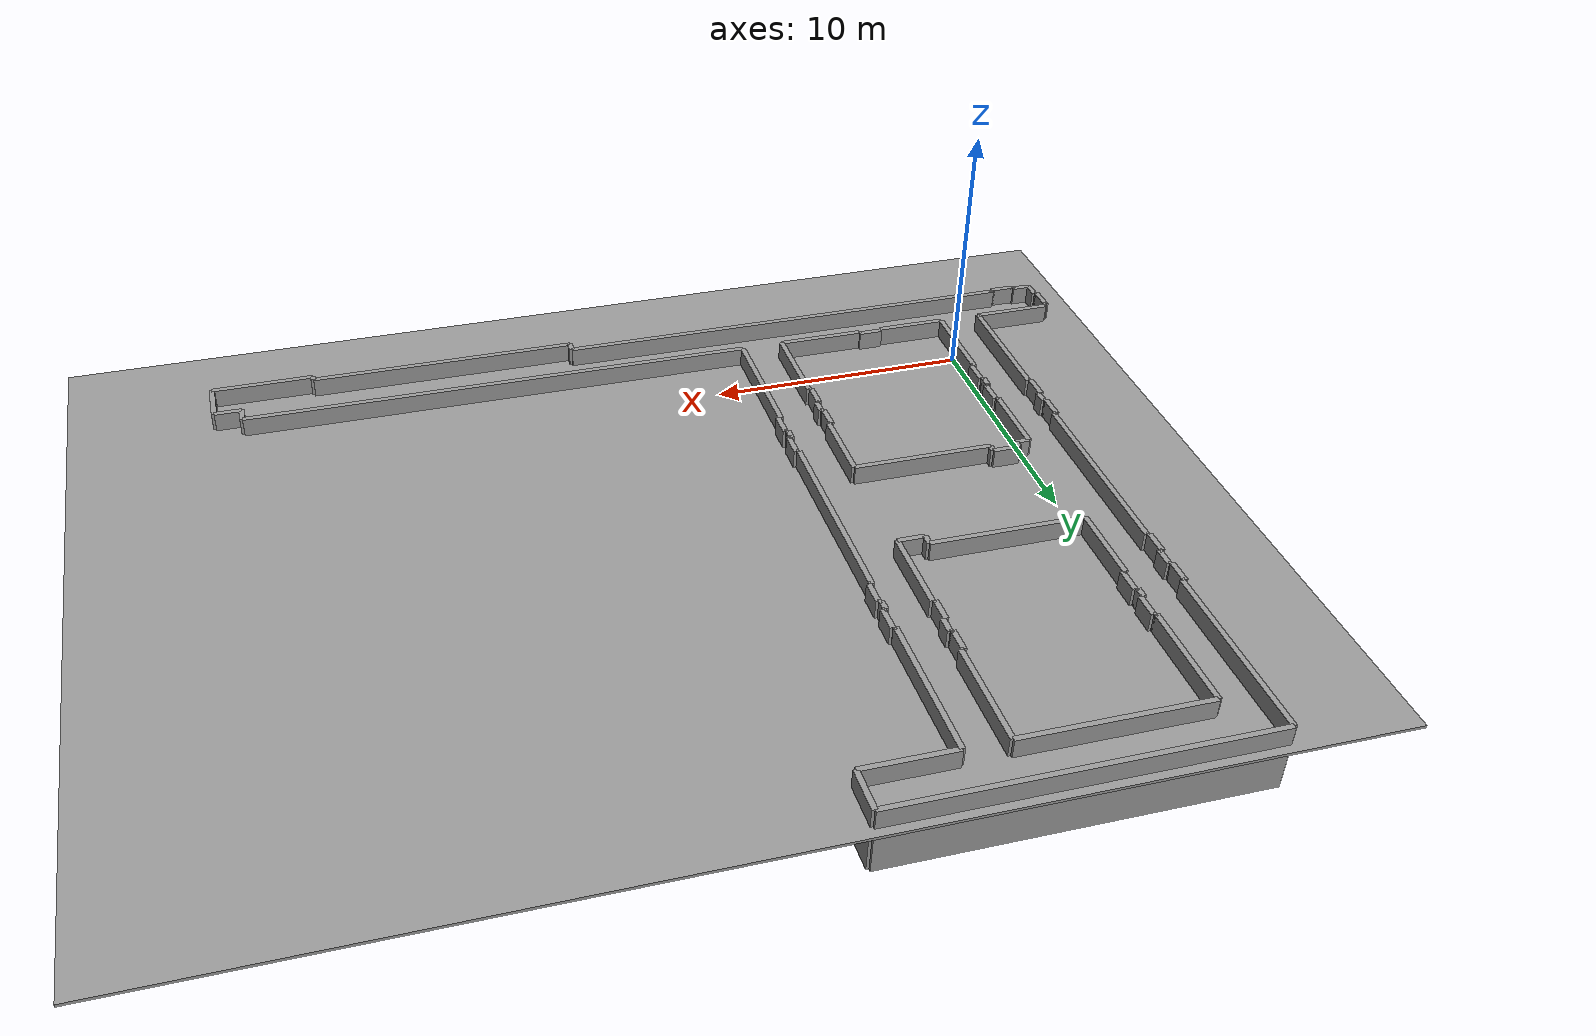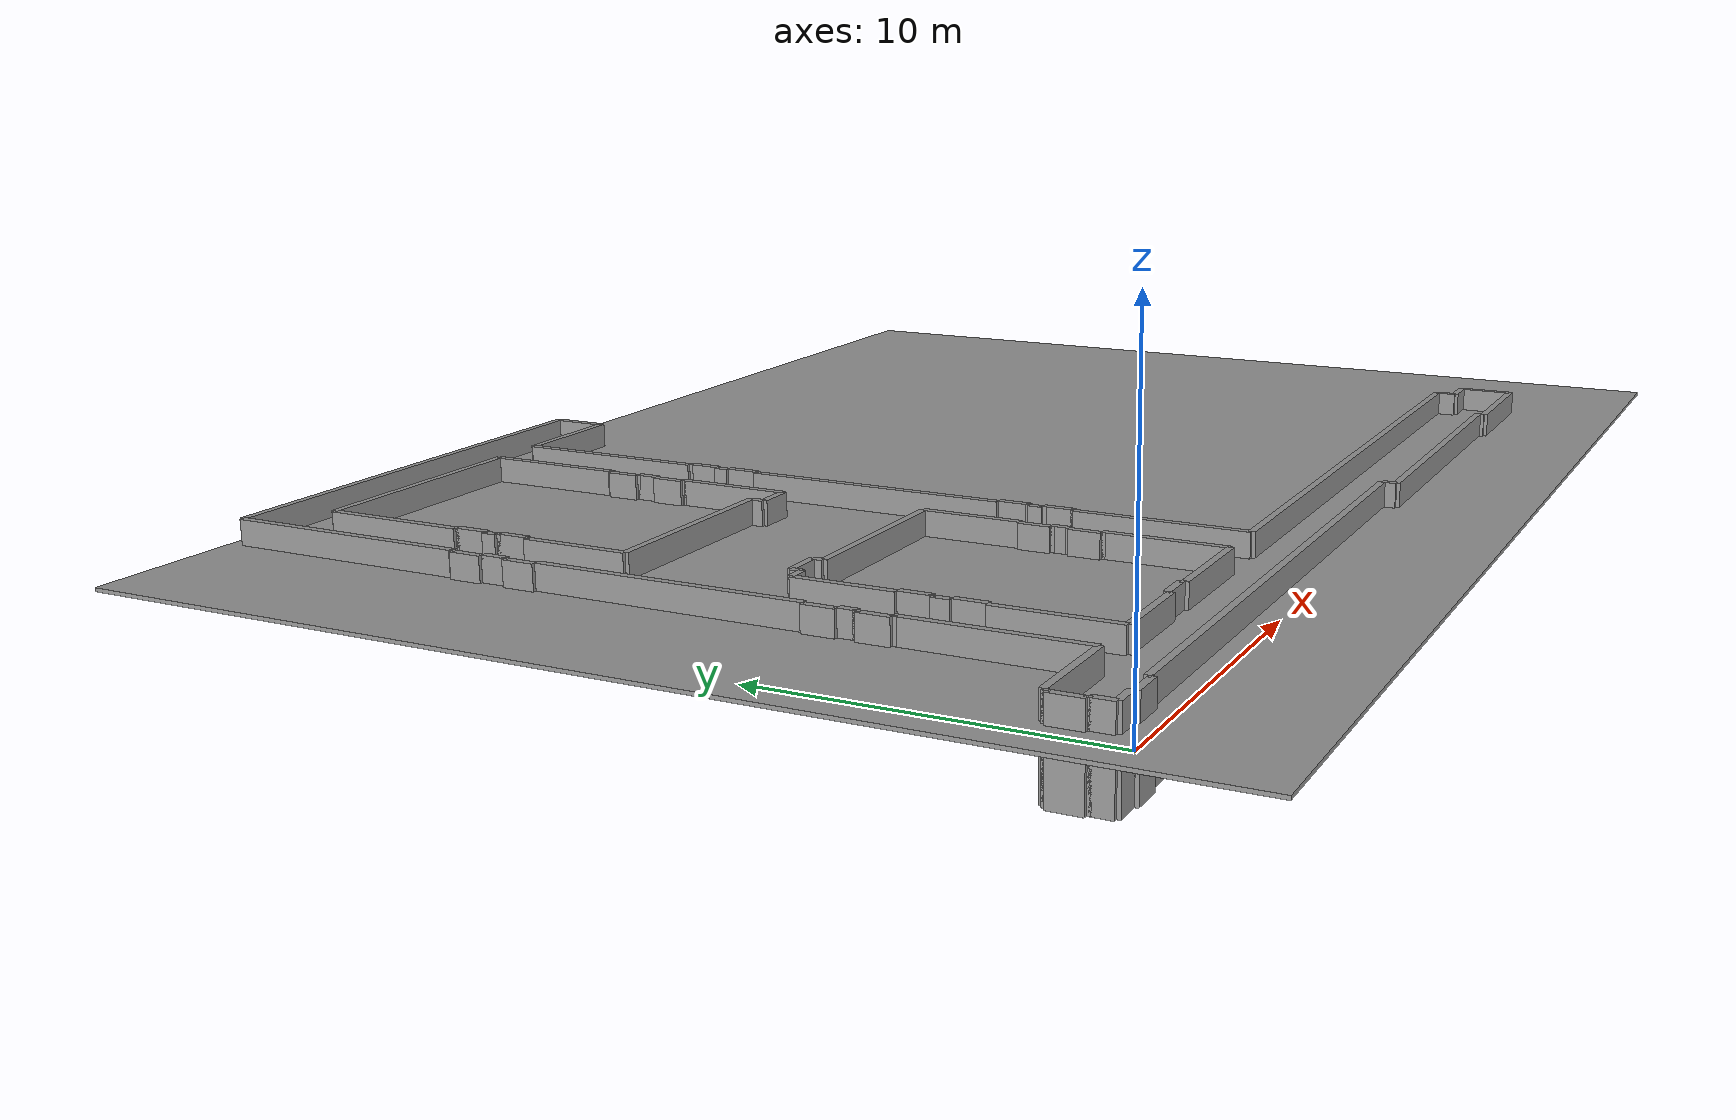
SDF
<?xml version='1.0'?>
<sdf version='1.4'>
  <model name='Levine'>
    <link name='Floor_0'>
      <collision name='Floor_0_Collision'>
        <geometry>
          <box>
            <size>40 30 0.1</size>
          </box>
        </geometry>
        <pose>0 0 0.05 0 -0 0</pose>
      </collision>
      <visual name='Floor_0_Visual'>
        <pose>0 0 0.05 0 -0 0</pose>
        <geometry>
          <box>
            <size>40 30 0.1</size>
          </box>
        </geometry>
        <material>
          <script>
            <uri>file://media/materials/scripts/gazebo.material</uri>
            <name>Gazebo/Grey</name>
          </script>
        </material>
      </visual>
      <velocity_decay>
        <linear>0</linear>
        <angular>0</angular>
      </velocity_decay>
      <pose>15 10 1.7 0 -0 0</pose>
    </link>
    <link name='Wall_0'>
      <collision name='Wall_0_Collision'>
        <geometry>
          <box>
            <size>4.9 0.2 2.5</size>
          </box>
        </geometry>
        <pose>0 0 1.25 0 0 0</pose>
      </collision>
      <visual name='Wall_0_Visual'>
        <pose>0 0 1.25 0 0 0</pose>
        <geometry>
          <box>
            <size>4.9 0.2 2.5</size>
          </box>
        </geometry>
        <material>
          <script>
            <uri>file://media/materials/scripts/gazebo.material</uri>
            <name>Gazebo/Grey</name>
          </script>
        </material>
      </visual>
      <velocity_decay>
        <linear>0</linear>
        <angular>0</angular>
      </velocity_decay>
      <pose>-0.6 3.05 0 0 0 1.57079632679</pose>
    </link>
    <link name='Wall_1'>
      <collision name='Wall_1_Collision'>
        <geometry>
          <box>
            <size>0.1 0.2 2.5</size>
          </box>
        </geometry>
        <pose>0 0 1.25 0 0 0</pose>
      </collision>
      <visual name='Wall_1_Visual'>
        <pose>0 0 1.25 0 0 0</pose>
        <geometry>
          <box>
            <size>0.1 0.2 2.5</size>
          </box>
        </geometry>
        <material>
          <script>
            <uri>file://media/materials/scripts/gazebo.material</uri>
            <name>Gazebo/Grey</name>
          </script>
        </material>
      </visual>
      <velocity_decay>
        <linear>0</linear>
        <angular>0</angular>
      </velocity_decay>
      <pose>-0.65 5.5 0 0 0 3.14159265359</pose>
    </link>
    <link name='Wall_2'>
      <collision name='Wall_2_Collision'>
        <geometry>
          <box>
            <size>0.9 0.2 2.5</size>
          </box>
        </geometry>
        <pose>0 0 1.25 0 0 0</pose>
      </collision>
      <visual name='Wall_2_Visual'>
        <pose>0 0 1.25 0 0 0</pose>
        <geometry>
          <box>
            <size>0.9 0.2 2.5</size>
          </box>
        </geometry>
        <material>
          <script>
            <uri>file://media/materials/scripts/gazebo.material</uri>
            <name>Gazebo/Grey</name>
          </script>
        </material>
      </visual>
      <velocity_decay>
        <linear>0</linear>
        <angular>0</angular>
      </velocity_decay>
      <pose>-0.7 5.95 0 0 0 1.57079632679</pose>
    </link>
    <link name='Wall_3'>
      <collision name='Wall_3_Collision'>
        <geometry>
          <box>
            <size>0.1 0.2 2.5</size>
          </box>
        </geometry>
        <pose>0 0 1.25 0 0 0</pose>
      </collision>
      <visual name='Wall_3_Visual'>
        <pose>0 0 1.25 0 0 0</pose>
        <geometry>
          <box>
            <size>0.1 0.2 2.5</size>
          </box>
        </geometry>
        <material>
          <script>
            <uri>file://media/materials/scripts/gazebo.material</uri>
            <name>Gazebo/Grey</name>
          </script>
        </material>
      </visual>
      <velocity_decay>
        <linear>0</linear>
        <angular>0</angular>
      </velocity_decay>
      <pose>-0.65 6.4 0 0 0 0.0</pose>
    </link>
    <link name='Wall_4'>
      <collision name='Wall_4_Collision'>
        <geometry>
          <box>
            <size>0.5 0.2 2.5</size>
          </box>
        </geometry>
        <pose>0 0 1.25 0 0 0</pose>
      </collision>
      <visual name='Wall_4_Visual'>
        <pose>0 0 1.25 0 0 0</pose>
        <geometry>
          <box>
            <size>0.5 0.2 2.5</size>
          </box>
        </geometry>
        <material>
          <script>
            <uri>file://media/materials/scripts/gazebo.material</uri>
            <name>Gazebo/Grey</name>
          </script>
        </material>
      </visual>
      <velocity_decay>
        <linear>0</linear>
        <angular>0</angular>
      </velocity_decay>
      <pose>-0.6 6.65 0 0 0 1.57079632679</pose>
    </link>
    <link name='Wall_5'>
      <collision name='Wall_5_Collision'>
        <geometry>
          <box>
            <size>0.1 0.2 2.5</size>
          </box>
        </geometry>
        <pose>0 0 1.25 0 0 0</pose>
      </collision>
      <visual name='Wall_5_Visual'>
        <pose>0 0 1.25 0 0 0</pose>
        <geometry>
          <box>
            <size>0.1 0.2 2.5</size>
          </box>
        </geometry>
        <material>
          <script>
            <uri>file://media/materials/scripts/gazebo.material</uri>
            <name>Gazebo/Grey</name>
          </script>
        </material>
      </visual>
      <velocity_decay>
        <linear>0</linear>
        <angular>0</angular>
      </velocity_decay>
      <pose>-0.65 6.9 0 0 0 3.14159265359</pose>
    </link>
    <link name='Wall_6'>
      <collision name='Wall_6_Collision'>
        <geometry>
          <box>
            <size>0.9 0.2 2.5</size>
          </box>
        </geometry>
        <pose>0 0 1.25 0 0 0</pose>
      </collision>
      <visual name='Wall_6_Visual'>
        <pose>0 0 1.25 0 0 0</pose>
        <geometry>
          <box>
            <size>0.9 0.2 2.5</size>
          </box>
        </geometry>
        <material>
          <script>
            <uri>file://media/materials/scripts/gazebo.material</uri>
            <name>Gazebo/Grey</name>
          </script>
        </material>
      </visual>
      <velocity_decay>
        <linear>0</linear>
        <angular>0</angular>
      </velocity_decay>
      <pose>-0.7 7.35 0 0 0 1.57079632679</pose>
    </link>
    <link name='Wall_7'>
      <collision name='Wall_7_Collision'>
        <geometry>
          <box>
            <size>0.1 0.2 2.5</size>
          </box>
        </geometry>
        <pose>0 0 1.25 0 0 0</pose>
      </collision>
      <visual name='Wall_7_Visual'>
        <pose>0 0 1.25 0 0 0</pose>
        <geometry>
          <box>
            <size>0.1 0.2 2.5</size>
          </box>
        </geometry>
        <material>
          <script>
            <uri>file://media/materials/scripts/gazebo.material</uri>
            <name>Gazebo/Grey</name>
          </script>
        </material>
      </visual>
      <velocity_decay>
        <linear>0</linear>
        <angular>0</angular>
      </velocity_decay>
      <pose>-0.65 7.8 0 0 0 0.0</pose>
    </link>
    <link name='Wall_8'>
      <collision name='Wall_8_Collision'>
        <geometry>
          <box>
            <size>7.4 0.2 2.5</size>
          </box>
        </geometry>
        <pose>0 0 1.25 0 0 0</pose>
      </collision>
      <visual name='Wall_8_Visual'>
        <pose>0 0 1.25 0 0 0</pose>
        <geometry>
          <box>
            <size>7.4 0.2 2.5</size>
          </box>
        </geometry>
        <material>
          <script>
            <uri>file://media/materials/scripts/gazebo.material</uri>
            <name>Gazebo/Grey</name>
          </script>
        </material>
      </visual>
      <velocity_decay>
        <linear>0</linear>
        <angular>0</angular>
      </velocity_decay>
      <pose>-0.6 11.5 0 0 0 1.57079632679</pose>
    </link>
    <link name='Wall_9'>
      <collision name='Wall_9_Collision'>
        <geometry>
          <box>
            <size>0.1 0.2 2.5</size>
          </box>
        </geometry>
        <pose>0 0 1.25 0 0 0</pose>
      </collision>
      <visual name='Wall_9_Visual'>
        <pose>0 0 1.25 0 0 0</pose>
        <geometry>
          <box>
            <size>0.1 0.2 2.5</size>
          </box>
        </geometry>
        <material>
          <script>
            <uri>file://media/materials/scripts/gazebo.material</uri>
            <name>Gazebo/Grey</name>
          </script>
        </material>
      </visual>
      <velocity_decay>
        <linear>0</linear>
        <angular>0</angular>
      </velocity_decay>
      <pose>-0.65 15.2 0 0 0 3.14159265359</pose>
    </link>
    <link name='Wall_10'>
      <collision name='Wall_10_Collision'>
        <geometry>
          <box>
            <size>0.9 0.2 2.5</size>
          </box>
        </geometry>
        <pose>0 0 1.25 0 0 0</pose>
      </collision>
      <visual name='Wall_10_Visual'>
        <pose>0 0 1.25 0 0 0</pose>
        <geometry>
          <box>
            <size>0.9 0.2 2.5</size>
          </box>
        </geometry>
        <material>
          <script>
            <uri>file://media/materials/scripts/gazebo.material</uri>
            <name>Gazebo/Grey</name>
          </script>
        </material>
      </visual>
      <velocity_decay>
        <linear>0</linear>
        <angular>0</angular>
      </velocity_decay>
      <pose>-0.7 15.65 0 0 0 1.57079632679</pose>
    </link>
    <link name='Wall_11'>
      <collision name='Wall_11_Collision'>
        <geometry>
          <box>
            <size>0.1 0.2 2.5</size>
          </box>
        </geometry>
        <pose>0 0 1.25 0 0 0</pose>
      </collision>
      <visual name='Wall_11_Visual'>
        <pose>0 0 1.25 0 0 0</pose>
        <geometry>
          <box>
            <size>0.1 0.2 2.5</size>
          </box>
        </geometry>
        <material>
          <script>
            <uri>file://media/materials/scripts/gazebo.material</uri>
            <name>Gazebo/Grey</name>
          </script>
        </material>
      </visual>
      <velocity_decay>
        <linear>0</linear>
        <angular>0</angular>
      </velocity_decay>
      <pose>-0.65 16.1 0 0 0 0.0</pose>
    </link>
    <link name='Wall_12'>
      <collision name='Wall_12_Collision'>
        <geometry>
          <box>
            <size>0.7 0.2 2.5</size>
          </box>
        </geometry>
        <pose>0 0 1.25 0 0 0</pose>
      </collision>
      <visual name='Wall_12_Visual'>
        <pose>0 0 1.25 0 0 0</pose>
        <geometry>
          <box>
            <size>0.7 0.2 2.5</size>
          </box>
        </geometry>
        <material>
          <script>
            <uri>file://media/materials/scripts/gazebo.material</uri>
            <name>Gazebo/Grey</name>
          </script>
        </material>
      </visual>
      <velocity_decay>
        <linear>0</linear>
        <angular>0</angular>
      </velocity_decay>
      <pose>-0.6 16.45 0 0 0 1.57079632679</pose>
    </link>
    <link name='Wall_13'>
      <collision name='Wall_13_Collision'>
        <geometry>
          <box>
            <size>0.1 0.2 2.5</size>
          </box>
        </geometry>
        <pose>0 0 1.25 0 0 0</pose>
      </collision>
      <visual name='Wall_13_Visual'>
        <pose>0 0 1.25 0 0 0</pose>
        <geometry>
          <box>
            <size>0.1 0.2 2.5</size>
          </box>
        </geometry>
        <material>
          <script>
            <uri>file://media/materials/scripts/gazebo.material</uri>
            <name>Gazebo/Grey</name>
          </script>
        </material>
      </visual>
      <velocity_decay>
        <linear>0</linear>
        <angular>0</angular>
      </velocity_decay>
      <pose>-0.65 16.8 0 0 0 3.14159265359</pose>
    </link>
    <link name='Wall_14'>
      <collision name='Wall_14_Collision'>
        <geometry>
          <box>
            <size>0.9 0.2 2.5</size>
          </box>
        </geometry>
        <pose>0 0 1.25 0 0 0</pose>
      </collision>
      <visual name='Wall_14_Visual'>
        <pose>0 0 1.25 0 0 0</pose>
        <geometry>
          <box>
            <size>0.9 0.2 2.5</size>
          </box>
        </geometry>
        <material>
          <script>
            <uri>file://media/materials/scripts/gazebo.material</uri>
            <name>Gazebo/Grey</name>
          </script>
        </material>
      </visual>
      <velocity_decay>
        <linear>0</linear>
        <angular>0</angular>
      </velocity_decay>
      <pose>-0.7 17.25 0 0 0 1.57079632679</pose>
    </link>
    <link name='Wall_15'>
      <collision name='Wall_15_Collision'>
        <geometry>
          <box>
            <size>0.1 0.2 2.5</size>
          </box>
        </geometry>
        <pose>0 0 1.25 0 0 0</pose>
      </collision>
      <visual name='Wall_15_Visual'>
        <pose>0 0 1.25 0 0 0</pose>
        <geometry>
          <box>
            <size>0.1 0.2 2.5</size>
          </box>
        </geometry>
        <material>
          <script>
            <uri>file://media/materials/scripts/gazebo.material</uri>
            <name>Gazebo/Grey</name>
          </script>
        </material>
      </visual>
      <velocity_decay>
        <linear>0</linear>
        <angular>0</angular>
      </velocity_decay>
      <pose>-0.65 17.7 0 0 0 0.0</pose>
    </link>
    <link name='Wall_16'>
      <collision name='Wall_16_Collision'>
        <geometry>
          <box>
            <size>6.9 0.2 2.5</size>
          </box>
        </geometry>
        <pose>0 0 1.25 0 0 0</pose>
      </collision>
      <visual name='Wall_16_Visual'>
        <pose>0 0 1.25 0 0 0</pose>
        <geometry>
          <box>
            <size>6.9 0.2 2.5</size>
          </box>
        </geometry>
        <material>
          <script>
            <uri>file://media/materials/scripts/gazebo.material</uri>
            <name>Gazebo/Grey</name>
          </script>
        </material>
      </visual>
      <velocity_decay>
        <linear>0</linear>
        <angular>0</angular>
      </velocity_decay>
      <pose>-0.6 21.15 0 0 0 1.57079632679</pose>
    </link>
    <link name='Wall_17'>
      <collision name='Wall_17_Collision'>
        <geometry>
          <box>
            <size>13.2 0.2 2.5</size>
          </box>
        </geometry>
        <pose>0 0 1.25 0 0 0</pose>
      </collision>
      <visual name='Wall_17_Visual'>
        <pose>0 0 1.25 0 0 0</pose>
        <geometry>
          <box>
            <size>13.2 0.2 2.5</size>
          </box>
        </geometry>
        <material>
          <script>
            <uri>file://media/materials/scripts/gazebo.material</uri>
            <name>Gazebo/Grey</name>
          </script>
        </material>
      </visual>
      <velocity_decay>
        <linear>0</linear>
        <angular>0</angular>
      </velocity_decay>
      <pose>6.0 24.6 0 0 0 0.0</pose>
    </link>
    <link name='Wall_18'>
      <collision name='Wall_18_Collision'>
        <geometry>
          <box>
            <size>1.6 0.2 2.5</size>
          </box>
        </geometry>
        <pose>0 0 1.25 0 0 0</pose>
      </collision>
      <visual name='Wall_18_Visual'>
        <pose>0 0 1.25 0 0 0</pose>
        <geometry>
          <box>
            <size>1.6 0.2 2.5</size>
          </box>
        </geometry>
        <material>
          <script>
            <uri>file://media/materials/scripts/gazebo.material</uri>
            <name>Gazebo/Grey</name>
          </script>
        </material>
      </visual>
      <velocity_decay>
        <linear>0</linear>
        <angular>0</angular>
      </velocity_decay>
      <pose>12.6 23.8 0 0 0 -1.57079632679</pose>
    </link>
    <link name='Wall_19'>
      <collision name='Wall_19_Collision'>
        <geometry>
          <box>
            <size>3.3 0.2 2.5</size>
          </box>
        </geometry>
        <pose>0 0 1.25 0 0 0</pose>
      </collision>
      <visual name='Wall_19_Visual'>
        <pose>0 0 1.25 0 0 0</pose>
        <geometry>
          <box>
            <size>3.3 0.2 2.5</size>
          </box>
        </geometry>
        <material>
          <script>
            <uri>file://media/materials/scripts/gazebo.material</uri>
            <name>Gazebo/Grey</name>
          </script>
        </material>
      </visual>
      <velocity_decay>
        <linear>0</linear>
        <angular>0</angular>
      </velocity_decay>
      <pose>10.95 23.0 0 0 0 3.14159265359</pose>
    </link>
    <link name='Wall_20'>
      <collision name='Wall_20_Collision'>
        <geometry>
          <box>
            <size>4.9 0.2 2.5</size>
          </box>
        </geometry>
        <pose>0 0 1.25 0 0 0</pose>
      </collision>
      <visual name='Wall_20_Visual'>
        <pose>0 0 1.25 0 0 0</pose>
        <geometry>
          <box>
            <size>4.9 0.2 2.5</size>
          </box>
        </geometry>
        <material>
          <script>
            <uri>file://media/materials/scripts/gazebo.material</uri>
            <name>Gazebo/Grey</name>
          </script>
        </material>
      </visual>
      <velocity_decay>
        <linear>0</linear>
        <angular>0</angular>
      </velocity_decay>
      <pose>9.3 3.05 0 0 0 1.57079632679</pose>
    </link>
    <link name='Wall_21'>
      <collision name='Wall_21_Collision'>
        <geometry>
          <box>
            <size>0.1 0.2 2.5</size>
          </box>
        </geometry>
        <pose>0 0 1.25 0 0 0</pose>
      </collision>
      <visual name='Wall_21_Visual'>
        <pose>0 0 1.25 0 0 0</pose>
        <geometry>
          <box>
            <size>0.1 0.2 2.5</size>
          </box>
        </geometry>
        <material>
          <script>
            <uri>file://media/materials/scripts/gazebo.material</uri>
            <name>Gazebo/Grey</name>
          </script>
        </material>
      </visual>
      <velocity_decay>
        <linear>0</linear>
        <angular>0</angular>
      </velocity_decay>
      <pose>9.35 5.5 0 0 0 0.0</pose>
    </link>
    <link name='Wall_22'>
      <collision name='Wall_22_Collision'>
        <geometry>
          <box>
            <size>0.9 0.2 2.5</size>
          </box>
        </geometry>
        <pose>0 0 1.25 0 0 0</pose>
      </collision>
      <visual name='Wall_22_Visual'>
        <pose>0 0 1.25 0 0 0</pose>
        <geometry>
          <box>
            <size>0.9 0.2 2.5</size>
          </box>
        </geometry>
        <material>
          <script>
            <uri>file://media/materials/scripts/gazebo.material</uri>
            <name>Gazebo/Grey</name>
          </script>
        </material>
      </visual>
      <velocity_decay>
        <linear>0</linear>
        <angular>0</angular>
      </velocity_decay>
      <pose>9.4 5.95 0 0 0 1.57079632679</pose>
    </link>
    <link name='Wall_23'>
      <collision name='Wall_23_Collision'>
        <geometry>
          <box>
            <size>0.1 0.2 2.5</size>
          </box>
        </geometry>
        <pose>0 0 1.25 0 0 0</pose>
      </collision>
      <visual name='Wall_23_Visual'>
        <pose>0 0 1.25 0 0 0</pose>
        <geometry>
          <box>
            <size>0.1 0.2 2.5</size>
          </box>
        </geometry>
        <material>
          <script>
            <uri>file://media/materials/scripts/gazebo.material</uri>
            <name>Gazebo/Grey</name>
          </script>
        </material>
      </visual>
      <velocity_decay>
        <linear>0</linear>
        <angular>0</angular>
      </velocity_decay>
      <pose>9.35 6.4 0 0 0 3.14159265359</pose>
    </link>
    <link name='Wall_24'>
      <collision name='Wall_24_Collision'>
        <geometry>
          <box>
            <size>0.4 0.2 2.5</size>
          </box>
        </geometry>
        <pose>0 0 1.25 0 0 0</pose>
      </collision>
      <visual name='Wall_24_Visual'>
        <pose>0 0 1.25 0 0 0</pose>
        <geometry>
          <box>
            <size>0.4 0.2 2.5</size>
          </box>
        </geometry>
        <material>
          <script>
            <uri>file://media/materials/scripts/gazebo.material</uri>
            <name>Gazebo/Grey</name>
          </script>
        </material>
      </visual>
      <velocity_decay>
        <linear>0</linear>
        <angular>0</angular>
      </velocity_decay>
      <pose>9.3 6.6 0 0 0 1.57079632679</pose>
    </link>
    <link name='Wall_25'>
      <collision name='Wall_25_Collision'>
        <geometry>
          <box>
            <size>0.1 0.2 2.5</size>
          </box>
        </geometry>
        <pose>0 0 1.25 0 0 0</pose>
      </collision>
      <visual name='Wall_25_Visual'>
        <pose>0 0 1.25 0 0 0</pose>
        <geometry>
          <box>
            <size>0.1 0.2 2.5</size>
          </box>
        </geometry>
        <material>
          <script>
            <uri>file://media/materials/scripts/gazebo.material</uri>
            <name>Gazebo/Grey</name>
          </script>
        </material>
      </visual>
      <velocity_decay>
        <linear>0</linear>
        <angular>0</angular>
      </velocity_decay>
      <pose>9.35 6.8 0 0 0 0.0</pose>
    </link>
    <link name='Wall_26'>
      <collision name='Wall_26_Collision'>
        <geometry>
          <box>
            <size>0.9 0.2 2.5</size>
          </box>
        </geometry>
        <pose>0 0 1.25 0 0 0</pose>
      </collision>
      <visual name='Wall_26_Visual'>
        <pose>0 0 1.25 0 0 0</pose>
        <geometry>
          <box>
            <size>0.9 0.2 2.5</size>
          </box>
        </geometry>
        <material>
          <script>
            <uri>file://media/materials/scripts/gazebo.material</uri>
            <name>Gazebo/Grey</name>
          </script>
        </material>
      </visual>
      <velocity_decay>
        <linear>0</linear>
        <angular>0</angular>
      </velocity_decay>
      <pose>9.4 7.25 0 0 0 1.57079632679</pose>
    </link>
    <link name='Wall_27'>
      <collision name='Wall_27_Collision'>
        <geometry>
          <box>
            <size>0.1 0.2 2.5</size>
          </box>
        </geometry>
        <pose>0 0 1.25 0 0 0</pose>
      </collision>
      <visual name='Wall_27_Visual'>
        <pose>0 0 1.25 0 0 0</pose>
        <geometry>
          <box>
            <size>0.1 0.2 2.5</size>
          </box>
        </geometry>
        <material>
          <script>
            <uri>file://media/materials/scripts/gazebo.material</uri>
            <name>Gazebo/Grey</name>
          </script>
        </material>
      </visual>
      <velocity_decay>
        <linear>0</linear>
        <angular>0</angular>
      </velocity_decay>
      <pose>9.35 7.7 0 0 0 3.14159265359</pose>
    </link>
    <link name='Wall_28'>
      <collision name='Wall_28_Collision'>
        <geometry>
          <box>
            <size>7.6 0.2 2.5</size>
          </box>
        </geometry>
        <pose>0 0 1.25 0 0 0</pose>
      </collision>
      <visual name='Wall_28_Visual'>
        <pose>0 0 1.25 0 0 0</pose>
        <geometry>
          <box>
            <size>7.6 0.2 2.5</size>
          </box>
        </geometry>
        <material>
          <script>
            <uri>file://media/materials/scripts/gazebo.material</uri>
            <name>Gazebo/Grey</name>
          </script>
        </material>
      </visual>
      <velocity_decay>
        <linear>0</linear>
        <angular>0</angular>
      </velocity_decay>
      <pose>9.3 11.5 0 0 0 1.57079632679</pose>
    </link>
    <link name='Wall_29'>
      <collision name='Wall_29_Collision'>
        <geometry>
          <box>
            <size>0.1 0.2 2.5</size>
          </box>
        </geometry>
        <pose>0 0 1.25 0 0 0</pose>
      </collision>
      <visual name='Wall_29_Visual'>
        <pose>0 0 1.25 0 0 0</pose>
        <geometry>
          <box>
            <size>0.1 0.2 2.5</size>
          </box>
        </geometry>
        <material>
          <script>
            <uri>file://media/materials/scripts/gazebo.material</uri>
            <name>Gazebo/Grey</name>
          </script>
        </material>
      </visual>
      <velocity_decay>
        <linear>0</linear>
        <angular>0</angular>
      </velocity_decay>
      <pose>9.35 15.3 0 0 0 0.0</pose>
    </link>
    <link name='Wall_30'>
      <collision name='Wall_30_Collision'>
        <geometry>
          <box>
            <size>0.9 0.2 2.5</size>
          </box>
        </geometry>
        <pose>0 0 1.25 0 0 0</pose>
      </collision>
      <visual name='Wall_30_Visual'>
        <pose>0 0 1.25 0 0 0</pose>
        <geometry>
          <box>
            <size>0.9 0.2 2.5</size>
          </box>
        </geometry>
        <material>
          <script>
            <uri>file://media/materials/scripts/gazebo.material</uri>
            <name>Gazebo/Grey</name>
          </script>
        </material>
      </visual>
      <velocity_decay>
        <linear>0</linear>
        <angular>0</angular>
      </velocity_decay>
      <pose>9.4 15.75 0 0 0 1.57079632679</pose>
    </link>
    <link name='Wall_31'>
      <collision name='Wall_31_Collision'>
        <geometry>
          <box>
            <size>0.1 0.2 2.5</size>
          </box>
        </geometry>
        <pose>0 0 1.25 0 0 0</pose>
      </collision>
      <visual name='Wall_31_Visual'>
        <pose>0 0 1.25 0 0 0</pose>
        <geometry>
          <box>
            <size>0.1 0.2 2.5</size>
          </box>
        </geometry>
        <material>
          <script>
            <uri>file://media/materials/scripts/gazebo.material</uri>
            <name>Gazebo/Grey</name>
          </script>
        </material>
      </visual>
      <velocity_decay>
        <linear>0</linear>
        <angular>0</angular>
      </velocity_decay>
      <pose>9.35 16.2 0 0 0 3.14159265359</pose>
    </link>
    <link name='Wall_32'>
      <collision name='Wall_32_Collision'>
        <geometry>
          <box>
            <size>0.4 0.2 2.5</size>
          </box>
        </geometry>
        <pose>0 0 1.25 0 0 0</pose>
      </collision>
      <visual name='Wall_32_Visual'>
        <pose>0 0 1.25 0 0 0</pose>
        <geometry>
          <box>
            <size>0.4 0.2 2.5</size>
          </box>
        </geometry>
        <material>
          <script>
            <uri>file://media/materials/scripts/gazebo.material</uri>
            <name>Gazebo/Grey</name>
          </script>
        </material>
      </visual>
      <velocity_decay>
        <linear>0</linear>
        <angular>0</angular>
      </velocity_decay>
      <pose>9.3 16.4 0 0 0 1.57079632679</pose>
    </link>
    <link name='Wall_33'>
      <collision name='Wall_33_Collision'>
        <geometry>
          <box>
            <size>0.1 0.2 2.5</size>
          </box>
        </geometry>
        <pose>0 0 1.25 0 0 0</pose>
      </collision>
      <visual name='Wall_33_Visual'>
        <pose>0 0 1.25 0 0 0</pose>
        <geometry>
          <box>
            <size>0.1 0.2 2.5</size>
          </box>
        </geometry>
        <material>
          <script>
            <uri>file://media/materials/scripts/gazebo.material</uri>
            <name>Gazebo/Grey</name>
          </script>
        </material>
      </visual>
      <velocity_decay>
        <linear>0</linear>
        <angular>0</angular>
      </velocity_decay>
      <pose>9.35 16.6 0 0 0 0.0</pose>
    </link>
    <link name='Wall_34'>
      <collision name='Wall_34_Collision'>
        <geometry>
          <box>
            <size>0.9 0.2 2.5</size>
          </box>
        </geometry>
        <pose>0 0 1.25 0 0 0</pose>
      </collision>
      <visual name='Wall_34_Visual'>
        <pose>0 0 1.25 0 0 0</pose>
        <geometry>
          <box>
            <size>0.9 0.2 2.5</size>
          </box>
        </geometry>
        <material>
          <script>
            <uri>file://media/materials/scripts/gazebo.material</uri>
            <name>Gazebo/Grey</name>
          </script>
        </material>
      </visual>
      <velocity_decay>
        <linear>0</linear>
        <angular>0</angular>
      </velocity_decay>
      <pose>9.4 17.05 0 0 0 1.57079632679</pose>
    </link>
    <link name='Wall_35'>
      <collision name='Wall_35_Collision'>
        <geometry>
          <box>
            <size>0.1 0.2 2.5</size>
          </box>
        </geometry>
        <pose>0 0 1.25 0 0 0</pose>
      </collision>
      <visual name='Wall_35_Visual'>
        <pose>0 0 1.25 0 0 0</pose>
        <geometry>
          <box>
            <size>0.1 0.2 2.5</size>
          </box>
        </geometry>
        <material>
          <script>
            <uri>file://media/materials/scripts/gazebo.material</uri>
            <name>Gazebo/Grey</name>
          </script>
        </material>
      </visual>
      <velocity_decay>
        <linear>0</linear>
        <angular>0</angular>
      </velocity_decay>
      <pose>9.35 17.5 0 0 0 3.14159265359</pose>
    </link>
    <link name='Wall_36'>
      <collision name='Wall_36_Collision'>
        <geometry>
          <box>
            <size>5.5 0.2 2.5</size>
          </box>
        </geometry>
        <pose>0 0 1.25 0 0 0</pose>
      </collision>
      <visual name='Wall_36_Visual'>
        <pose>0 0 1.25 0 0 0</pose>
        <geometry>
          <box>
            <size>5.5 0.2 2.5</size>
          </box>
        </geometry>
        <material>
          <script>
            <uri>file://media/materials/scripts/gazebo.material</uri>
            <name>Gazebo/Grey</name>
          </script>
        </material>
      </visual>
      <velocity_decay>
        <linear>0</linear>
        <angular>0</angular>
      </velocity_decay>
      <pose>9.3 20.25 0 0 0 1.57079632679</pose>
    </link>
    <link name='Wall_37'>
      <collision name='Wall_37_Collision'>
        <geometry>
          <box>
            <size>2.9 0.2 2.5</size>
          </box>
        </geometry>
        <pose>0 0 1.25 0 0 0</pose>
      </collision>
      <visual name='Wall_37_Visual'>
        <pose>0 0 1.25 0 0 0</pose>
        <geometry>
          <box>
            <size>2.9 0.2 2.5</size>
          </box>
        </geometry>
        <material>
          <script>
            <uri>file://media/materials/scripts/gazebo.material</uri>
            <name>Gazebo/Grey</name>
          </script>
        </material>
      </visual>
      <velocity_decay>
        <linear>0</linear>
        <angular>0</angular>
      </velocity_decay>
      <pose>-2.05 0.6 0 0 0 3.14159265359</pose>
    </link>
    <link name='Wall_38'>
      <collision name='Wall_38_Collision'>
        <geometry>
          <box>
            <size>0.1 0.2 2.5</size>
          </box>
        </geometry>
        <pose>0 0 1.25 0 0 0</pose>
      </collision>
      <visual name='Wall_38_Visual'>
        <pose>0 0 1.25 0 0 0</pose>
        <geometry>
          <box>
            <size>0.1 0.2 2.5</size>
          </box>
        </geometry>
        <material>
          <script>
            <uri>file://media/materials/scripts/gazebo.material</uri>
            <name>Gazebo/Grey</name>
          </script>
        </material>
      </visual>
      <velocity_decay>
        <linear>0</linear>
        <angular>0</angular>
      </velocity_decay>
      <pose>-3.5 0.55 0 0 0 -1.57079632679</pose>
    </link>
    <link name='Wall_39'>
      <collision name='Wall_39_Collision'>
        <geometry>
          <box>
            <size>0.1 0.2 2.5</size>
          </box>
        </geometry>
        <pose>0 0 1.25 0 0 0</pose>
      </collision>
      <visual name='Wall_39_Visual'>
        <pose>0 0 1.25 0 0 0</pose>
        <geometry>
          <box>
            <size>0.1 0.2 2.5</size>
          </box>
        </geometry>
        <material>
          <script>
            <uri>file://media/materials/scripts/gazebo.material</uri>
            <name>Gazebo/Grey</name>
          </script>
        </material>
      </visual>
      <velocity_decay>
        <linear>0</linear>
        <angular>0</angular>
      </velocity_decay>
      <pose>-3.55 0.5 0 0 0 3.14159265359</pose>
    </link>
    <link name='Wall_40'>
      <collision name='Wall_40_Collision'>
        <geometry>
          <box>
            <size>0.9 0.2 2.5</size>
          </box>
        </geometry>
        <pose>0 0 1.25 0 0 0</pose>
      </collision>
      <visual name='Wall_40_Visual'>
        <pose>0 0 1.25 0 0 0</pose>
        <geometry>
          <box>
            <size>0.9 0.2 2.5</size>
          </box>
        </geometry>
        <material>
          <script>
            <uri>file://media/materials/scripts/gazebo.material</uri>
            <name>Gazebo/Grey</name>
          </script>
        </material>
      </visual>
      <velocity_decay>
        <linear>0</linear>
        <angular>0</angular>
      </velocity_decay>
      <pose>-3.6 0.05 0 0 0 -1.57079632679</pose>
    </link>
    <link name='Wall_41'>
      <collision name='Wall_41_Collision'>
        <geometry>
          <box>
            <size>0.1 0.2 2.5</size>
          </box>
        </geometry>
        <pose>0 0 1.25 0 0 0</pose>
      </collision>
      <visual name='Wall_41_Visual'>
        <pose>0 0 1.25 0 0 0</pose>
        <geometry>
          <box>
            <size>0.1 0.2 2.5</size>
          </box>
        </geometry>
        <material>
          <script>
            <uri>file://media/materials/scripts/gazebo.material</uri>
            <name>Gazebo/Grey</name>
          </script>
        </material>
      </visual>
      <velocity_decay>
        <linear>0</linear>
        <angular>0</angular>
      </velocity_decay>
      <pose>-3.55 -0.4 0 0 0 0.0</pose>
    </link>
    <link name='Wall_42'>
      <collision name='Wall_42_Collision'>
        <geometry>
          <box>
            <size>0.6 0.2 2.5</size>
          </box>
        </geometry>
        <pose>0 0 1.25 0 0 0</pose>
      </collision>
      <visual name='Wall_42_Visual'>
        <pose>0 0 1.25 0 0 0</pose>
        <geometry>
          <box>
            <size>0.6 0.2 2.5</size>
          </box>
        </geometry>
        <material>
          <script>
            <uri>file://media/materials/scripts/gazebo.material</uri>
            <name>Gazebo/Grey</name>
          </script>
        </material>
      </visual>
      <velocity_decay>
        <linear>0</linear>
        <angular>0</angular>
      </velocity_decay>
      <pose>-3.5 -0.7 0 0 0 -1.57079632679</pose>
    </link>
    <link name='Wall_43'>
      <collision name='Wall_43_Collision'>
        <geometry>
          <box>
            <size>0.7 0.2 2.5</size>
          </box>
        </geometry>
        <pose>0 0 1.25 0 0 0</pose>
      </collision>
      <visual name='Wall_43_Visual'>
        <pose>0 0 1.25 0 0 0</pose>
        <geometry>
          <box>
            <size>0.7 0.2 2.5</size>
          </box>
        </geometry>
        <material>
          <script>
            <uri>file://media/materials/scripts/gazebo.material</uri>
            <name>Gazebo/Grey</name>
          </script>
        </material>
      </visual>
      <velocity_decay>
        <linear>0</linear>
        <angular>0</angular>
      </velocity_decay>
      <pose>-3.15 -1.0 0 0 0 0.0</pose>
    </link>
    <link name='Wall_44'>
      <collision name='Wall_44_Collision'>
        <geometry>
          <box>
            <size>0.1 0.2 2.5</size>
          </box>
        </geometry>
        <pose>0 0 1.25 0 0 0</pose>
      </collision>
      <visual name='Wall_44_Visual'>
        <pose>0 0 1.25 0 0 0</pose>
        <geometry>
          <box>
            <size>0.1 0.2 2.5</size>
          </box>
        </geometry>
        <material>
          <script>
            <uri>file://media/materials/scripts/gazebo.material</uri>
            <name>Gazebo/Grey</name>
          </script>
        </material>
      </visual>
      <velocity_decay>
        <linear>0</linear>
        <angular>0</angular>
      </velocity_decay>
      <pose>-2.8 -1.05 0 0 0 -1.57079632679</pose>
    </link>
    <link name='Wall_45'>
      <collision name='Wall_45_Collision'>
        <geometry>
          <box>
            <size>0.9 0.2 2.5</size>
          </box>
        </geometry>
        <pose>0 0 1.25 0 0 0</pose>
      </collision>
      <visual name='Wall_45_Visual'>
        <pose>0 0 1.25 0 0 0</pose>
        <geometry>
          <box>
            <size>0.9 0.2 2.5</size>
          </box>
        </geometry>
        <material>
          <script>
            <uri>file://media/materials/scripts/gazebo.material</uri>
            <name>Gazebo/Grey</name>
          </script>
        </material>
      </visual>
      <velocity_decay>
        <linear>0</linear>
        <angular>0</angular>
      </velocity_decay>
      <pose>-2.35 -1.1 0 0 0 0.0</pose>
    </link>
    <link name='Wall_46'>
      <collision name='Wall_46_Collision'>
        <geometry>
          <box>
            <size>0.1 0.2 2.5</size>
          </box>
        </geometry>
        <pose>0 0 1.25 0 0 0</pose>
      </collision>
      <visual name='Wall_46_Visual'>
        <pose>0 0 1.25 0 0 0</pose>
        <geometry>
          <box>
            <size>0.1 0.2 2.5</size>
          </box>
        </geometry>
        <material>
          <script>
            <uri>file://media/materials/scripts/gazebo.material</uri>
            <name>Gazebo/Grey</name>
          </script>
        </material>
      </visual>
      <velocity_decay>
        <linear>0</linear>
        <angular>0</angular>
      </velocity_decay>
      <pose>-1.9 -1.05 0 0 0 1.57079632679</pose>
    </link>
    <link name='Wall_47'>
      <collision name='Wall_47_Collision'>
        <geometry>
          <box>
            <size>17.7 0.2 2.5</size>
          </box>
        </geometry>
        <pose>0 0 1.25 0 0 0</pose>
      </collision>
      <visual name='Wall_47_Visual'>
        <pose>0 0 1.25 0 0 0</pose>
        <geometry>
          <box>
            <size>17.7 0.2 2.5</size>
          </box>
        </geometry>
        <material>
          <script>
            <uri>file://media/materials/scripts/gazebo.material</uri>
            <name>Gazebo/Grey</name>
          </script>
        </material>
      </visual>
      <velocity_decay>
        <linear>0</linear>
        <angular>0</angular>
      </velocity_decay>
      <pose>6.95 -1.0 0 0 0 0.0</pose>
    </link>
    <link name='Wall_48'>
      <collision name='Wall_48_Collision'>
        <geometry>
          <box>
            <size>0.4 0.2 2.5</size>
          </box>
        </geometry>
        <pose>0 0 1.25 0 0 0</pose>
      </collision>
      <visual name='Wall_48_Visual'>
        <pose>0 0 1.25 0 0 0</pose>
        <geometry>
          <box>
            <size>0.4 0.2 2.5</size>
          </box>
        </geometry>
        <material>
          <script>
            <uri>file://media/materials/scripts/gazebo.material</uri>
            <name>Gazebo/Grey</name>
          </script>
        </material>
      </visual>
      <velocity_decay>
        <linear>0</linear>
        <angular>0</angular>
      </velocity_decay>
      <pose>15.8 -1.2 0 0 0 -1.57079632679</pose>
    </link>
    <link name='Wall_49'>
      <collision name='Wall_49_Collision'>
        <geometry>
          <box>
            <size>10.0 0.2 2.5</size>
          </box>
        </geometry>
        <pose>0 0 1.25 0 0 0</pose>
      </collision>
      <visual name='Wall_49_Visual'>
        <pose>0 0 1.25 0 0 0</pose>
        <geometry>
          <box>
            <size>10.0 0.2 2.5</size>
          </box>
        </geometry>
        <material>
          <script>
            <uri>file://media/materials/scripts/gazebo.material</uri>
            <name>Gazebo/Grey</name>
          </script>
        </material>
      </visual>
      <velocity_decay>
        <linear>0</linear>
        <angular>0</angular>
      </velocity_decay>
      <pose>20.8 -1.4 0 0 0 0.0</pose>
    </link>
    <link name='Wall_50'>
      <collision name='Wall_50_Collision'>
        <geometry>
          <box>
            <size>0.2 0.2 2.5</size>
          </box>
        </geometry>
        <pose>0 0 1.25 0 0 0</pose>
      </collision>
      <visual name='Wall_50_Visual'>
        <pose>0 0 1.25 0 0 0</pose>
        <geometry>
          <box>
            <size>0.2 0.2 2.5</size>
          </box>
        </geometry>
        <material>
          <script>
            <uri>file://media/materials/scripts/gazebo.material</uri>
            <name>Gazebo/Grey</name>
          </script>
        </material>
      </visual>
      <velocity_decay>
        <linear>0</linear>
        <angular>0</angular>
      </velocity_decay>
      <pose>25.8 -1.5 0 0 0 -1.57079632679</pose>
    </link>
    <link name='Wall_51'>
      <collision name='Wall_51_Collision'>
        <geometry>
          <box>
            <size>3.8 0.2 2.5</size>
          </box>
        </geometry>
        <pose>0 0 1.25 0 0 0</pose>
      </collision>
      <visual name='Wall_51_Visual'>
        <pose>0 0 1.25 0 0 0</pose>
        <geometry>
          <box>
            <size>3.8 0.2 2.5</size>
          </box>
        </geometry>
        <material>
          <script>
            <uri>file://media/materials/scripts/gazebo.material</uri>
            <name>Gazebo/Grey</name>
          </script>
        </material>
      </visual>
      <velocity_decay>
        <linear>0</linear>
        <angular>0</angular>
      </velocity_decay>
      <pose>27.7 -1.6 0 0 0 0.0</pose>
    </link>
    <link name='Wall_52'>
      <collision name='Wall_52_Collision'>
        <geometry>
          <box>
            <size>1.6 0.2 2.5</size>
          </box>
        </geometry>
        <pose>0 0 1.25 0 0 0</pose>
      </collision>
      <visual name='Wall_52_Visual'>
        <pose>0 0 1.25 0 0 0</pose>
        <geometry>
          <box>
            <size>1.6 0.2 2.5</size>
          </box>
        </geometry>
        <material>
          <script>
            <uri>file://media/materials/scripts/gazebo.material</uri>
            <name>Gazebo/Grey</name>
          </script>
        </material>
      </visual>
      <velocity_decay>
        <linear>0</linear>
        <angular>0</angular>
      </velocity_decay>
      <pose>29.6 -0.8 0 0 0 1.57079632679</pose>
    </link>
    <link name='Wall_53'>
      <collision name='Wall_53_Collision'>
        <geometry>
          <box>
            <size>1.0 0.2 2.5</size>
          </box>
        </geometry>
        <pose>0 0 1.25 0 0 0</pose>
      </collision>
      <visual name='Wall_53_Visual'>
        <pose>0 0 1.25 0 0 0</pose>
        <geometry>
          <box>
            <size>1.0 0.2 2.5</size>
          </box>
        </geometry>
        <material>
          <script>
            <uri>file://media/materials/scripts/gazebo.material</uri>
            <name>Gazebo/Grey</name>
          </script>
        </material>
      </visual>
      <velocity_decay>
        <linear>0</linear>
        <angular>0</angular>
      </velocity_decay>
      <pose>29.1 0.0 0 0 0 3.14159265359</pose>
    </link>
    <link name='Wall_54'>
      <collision name='Wall_54_Collision'>
        <geometry>
          <box>
            <size>0.6 0.2 2.5</size>
          </box>
        </geometry>
        <pose>0 0 1.25 0 0 0</pose>
      </collision>
      <visual name='Wall_54_Visual'>
        <pose>0 0 1.25 0 0 0</pose>
        <geometry>
          <box>
            <size>0.6 0.2 2.5</size>
          </box>
        </geometry>
        <material>
          <script>
            <uri>file://media/materials/scripts/gazebo.material</uri>
            <name>Gazebo/Grey</name>
          </script>
        </material>
      </visual>
      <velocity_decay>
        <linear>0</linear>
        <angular>0</angular>
      </velocity_decay>
      <pose>28.6 0.3 0 0 0 1.57079632679</pose>
    </link>
    <link name='Wall_55'>
      <collision name='Wall_55_Collision'>
        <geometry>
          <box>
            <size>19.3 0.2 2.5</size>
          </box>
        </geometry>
        <pose>0 0 1.25 0 0 0</pose>
      </collision>
      <visual name='Wall_55_Visual'>
        <pose>0 0 1.25 0 0 0</pose>
        <geometry>
          <box>
            <size>19.3 0.2 2.5</size>
          </box>
        </geometry>
        <material>
          <script>
            <uri>file://media/materials/scripts/gazebo.material</uri>
            <name>Gazebo/Grey</name>
          </script>
        </material>
      </visual>
      <velocity_decay>
        <linear>0</linear>
        <angular>0</angular>
      </velocity_decay>
      <pose>18.95 0.6 0 0 0 3.14159265359</pose>
    </link>
    <link name='Wall_56'>
      <collision name='Wall_56_Collision'>
        <geometry>
          <box>
            <size>3.4 0.2 2.5</size>
          </box>
        </geometry>
        <pose>0 0 1.25 0 0 0</pose>
      </collision>
      <visual name='Wall_56_Visual'>
        <pose>0 0 1.25 0 0 0</pose>
        <geometry>
          <box>
            <size>3.4 0.2 2.5</size>
          </box>
        </geometry>
        <material>
          <script>
            <uri>file://media/materials/scripts/gazebo.material</uri>
            <name>Gazebo/Grey</name>
          </script>
        </material>
      </visual>
      <velocity_decay>
        <linear>0</linear>
        <angular>0</angular>
      </velocity_decay>
      <pose>1.0 2.3 0 0 0 1.57079632679</pose>
    </link>
    <link name='Wall_57'>
      <collision name='Wall_57_Collision'>
        <geometry>
          <box>
            <size>0.1 0.2 2.5</size>
          </box>
        </geometry>
        <pose>0 0 1.25 0 0 0</pose>
      </collision>
      <visual name='Wall_57_Visual'>
        <pose>0 0 1.25 0 0 0</pose>
        <geometry>
          <box>
            <size>0.1 0.2 2.5</size>
          </box>
        </geometry>
        <material>
          <script>
            <uri>file://media/materials/scripts/gazebo.material</uri>
            <name>Gazebo/Grey</name>
          </script>
        </material>
      </visual>
      <velocity_decay>
        <linear>0</linear>
        <angular>0</angular>
      </velocity_decay>
      <pose>1.05 4.0 0 0 0 0.0</pose>
    </link>
    <link name='Wall_58'>
      <collision name='Wall_58_Collision'>
        <geometry>
          <box>
            <size>0.9 0.2 2.5</size>
          </box>
        </geometry>
        <pose>0 0 1.25 0 0 0</pose>
      </collision>
      <visual name='Wall_58_Visual'>
        <pose>0 0 1.25 0 0 0</pose>
        <geometry>
          <box>
            <size>0.9 0.2 2.5</size>
          </box>
        </geometry>
        <material>
          <script>
            <uri>file://media/materials/scripts/gazebo.material</uri>
            <name>Gazebo/Grey</name>
          </script>
        </material>
      </visual>
      <velocity_decay>
        <linear>0</linear>
        <angular>0</angular>
      </velocity_decay>
      <pose>1.1 4.45 0 0 0 1.57079632679</pose>
    </link>
    <link name='Wall_59'>
      <collision name='Wall_59_Collision'>
        <geometry>
          <box>
            <size>0.1 0.2 2.5</size>
          </box>
        </geometry>
        <pose>0 0 1.25 0 0 0</pose>
      </collision>
      <visual name='Wall_59_Visual'>
        <pose>0 0 1.25 0 0 0</pose>
        <geometry>
          <box>
            <size>0.1 0.2 2.5</size>
          </box>
        </geometry>
        <material>
          <script>
            <uri>file://media/materials/scripts/gazebo.material</uri>
            <name>Gazebo/Grey</name>
          </script>
        </material>
      </visual>
      <velocity_decay>
        <linear>0</linear>
        <angular>0</angular>
      </velocity_decay>
      <pose>1.05 4.9 0 0 0 3.14159265359</pose>
    </link>
    <link name='Wall_60'>
      <collision name='Wall_60_Collision'>
        <geometry>
          <box>
            <size>0.5 0.2 2.5</size>
          </box>
        </geometry>
        <pose>0 0 1.25 0 0 0</pose>
      </collision>
      <visual name='Wall_60_Visual'>
        <pose>0 0 1.25 0 0 0</pose>
        <geometry>
          <box>
            <size>0.5 0.2 2.5</size>
          </box>
        </geometry>
        <material>
          <script>
            <uri>file://media/materials/scripts/gazebo.material</uri>
            <name>Gazebo/Grey</name>
          </script>
        </material>
      </visual>
      <velocity_decay>
        <linear>0</linear>
        <angular>0</angular>
      </velocity_decay>
      <pose>1.0 5.15 0 0 0 1.57079632679</pose>
    </link>
    <link name='Wall_61'>
      <collision name='Wall_61_Collision'>
        <geometry>
          <box>
            <size>0.1 0.2 2.5</size>
          </box>
        </geometry>
        <pose>0 0 1.25 0 0 0</pose>
      </collision>
      <visual name='Wall_61_Visual'>
        <pose>0 0 1.25 0 0 0</pose>
        <geometry>
          <box>
            <size>0.1 0.2 2.5</size>
          </box>
        </geometry>
        <material>
          <script>
            <uri>file://media/materials/scripts/gazebo.material</uri>
            <name>Gazebo/Grey</name>
          </script>
        </material>
      </visual>
      <velocity_decay>
        <linear>0</linear>
        <angular>0</angular>
      </velocity_decay>
      <pose>1.05 5.4 0 0 0 0.0</pose>
    </link>
    <link name='Wall_62'>
      <collision name='Wall_62_Collision'>
        <geometry>
          <box>
            <size>0.9 0.2 2.5</size>
          </box>
        </geometry>
        <pose>0 0 1.25 0 0 0</pose>
      </collision>
      <visual name='Wall_62_Visual'>
        <pose>0 0 1.25 0 0 0</pose>
        <geometry>
          <box>
            <size>0.9 0.2 2.5</size>
          </box>
        </geometry>
        <material>
          <script>
            <uri>file://media/materials/scripts/gazebo.material</uri>
            <name>Gazebo/Grey</name>
          </script>
        </material>
      </visual>
      <velocity_decay>
        <linear>0</linear>
        <angular>0</angular>
      </velocity_decay>
      <pose>1.1 5.85 0 0 0 1.57079632679</pose>
    </link>
    <link name='Wall_63'>
      <collision name='Wall_63_Collision'>
        <geometry>
          <box>
            <size>0.1 0.2 2.5</size>
          </box>
        </geometry>
        <pose>0 0 1.25 0 0 0</pose>
      </collision>
      <visual name='Wall_63_Visual'>
        <pose>0 0 1.25 0 0 0</pose>
        <geometry>
          <box>
            <size>0.1 0.2 2.5</size>
          </box>
        </geometry>
        <material>
          <script>
            <uri>file://media/materials/scripts/gazebo.material</uri>
            <name>Gazebo/Grey</name>
          </script>
        </material>
      </visual>
      <velocity_decay>
        <linear>0</linear>
        <angular>0</angular>
      </velocity_decay>
      <pose>1.05 6.3 0 0 0 3.14159265359</pose>
    </link>
    <link name='Wall_64'>
      <collision name='Wall_64_Collision'>
        <geometry>
          <box>
            <size>2.8 0.2 2.5</size>
          </box>
        </geometry>
        <pose>0 0 1.25 0 0 0</pose>
      </collision>
      <visual name='Wall_64_Visual'>
        <pose>0 0 1.25 0 0 0</pose>
        <geometry>
          <box>
            <size>2.8 0.2 2.5</size>
          </box>
        </geometry>
        <material>
          <script>
            <uri>file://media/materials/scripts/gazebo.material</uri>
            <name>Gazebo/Grey</name>
          </script>
        </material>
      </visual>
      <velocity_decay>
        <linear>0</linear>
        <angular>0</angular>
      </velocity_decay>
      <pose>1.0 7.7 0 0 0 1.57079632679</pose>
    </link>
    <link name='Wall_65'>
      <collision name='Wall_65_Collision'>
        <geometry>
          <box>
            <size>0.5 0.2 2.5</size>
          </box>
        </geometry>
        <pose>0 0 1.25 0 0 0</pose>
      </collision>
      <visual name='Wall_65_Visual'>
        <pose>0 0 1.25 0 0 0</pose>
        <geometry>
          <box>
            <size>0.5 0.2 2.5</size>
          </box>
        </geometry>
        <material>
          <script>
            <uri>file://media/materials/scripts/gazebo.material</uri>
            <name>Gazebo/Grey</name>
          </script>
        </material>
      </visual>
      <velocity_decay>
        <linear>0</linear>
        <angular>0</angular>
      </velocity_decay>
      <pose>1.25 9.1 0 0 0 0.0</pose>
    </link>
    <link name='Wall_66'>
      <collision name='Wall_66_Collision'>
        <geometry>
          <box>
            <size>0.3 0.2 2.5</size>
          </box>
        </geometry>
        <pose>0 0 1.25 0 0 0</pose>
      </collision>
      <visual name='Wall_66_Visual'>
        <pose>0 0 1.25 0 0 0</pose>
        <geometry>
          <box>
            <size>0.3 0.2 2.5</size>
          </box>
        </geometry>
        <material>
          <script>
            <uri>file://media/materials/scripts/gazebo.material</uri>
            <name>Gazebo/Grey</name>
          </script>
        </material>
      </visual>
      <velocity_decay>
        <linear>0</linear>
        <angular>0</angular>
      </velocity_decay>
      <pose>1.5 9.25 0 0 0 1.57079632679</pose>
    </link>
    <link name='Wall_67'>
      <collision name='Wall_67_Collision'>
        <geometry>
          <box>
            <size>1.0 0.2 2.5</size>
          </box>
        </geometry>
        <pose>0 0 1.25 0 0 0</pose>
      </collision>
      <visual name='Wall_67_Visual'>
        <pose>0 0 1.25 0 0 0</pose>
        <geometry>
          <box>
            <size>1.0 0.2 2.5</size>
          </box>
        </geometry>
        <material>
          <script>
            <uri>file://media/materials/scripts/gazebo.material</uri>
            <name>Gazebo/Grey</name>
          </script>
        </material>
      </visual>
      <velocity_decay>
        <linear>0</linear>
        <angular>0</angular>
      </velocity_decay>
      <pose>2.0 9.4 0 0 0 0.0</pose>
    </link>
    <link name='Wall_68'>
      <collision name='Wall_68_Collision'>
        <geometry>
          <box>
            <size>0.3 0.2 2.5</size>
          </box>
        </geometry>
        <pose>0 0 1.25 0 0 0</pose>
      </collision>
      <visual name='Wall_68_Visual'>
        <pose>0 0 1.25 0 0 0</pose>
        <geometry>
          <box>
            <size>0.3 0.2 2.5</size>
          </box>
        </geometry>
        <material>
          <script>
            <uri>file://media/materials/scripts/gazebo.material</uri>
            <name>Gazebo/Grey</name>
          </script>
        </material>
      </visual>
      <velocity_decay>
        <linear>0</linear>
        <angular>0</angular>
      </velocity_decay>
      <pose>2.5 9.25 0 0 0 -1.57079632679</pose>
    </link>
    <link name='Wall_69'>
      <collision name='Wall_69_Collision'>
        <geometry>
          <box>
            <size>5.2 0.2 2.5</size>
          </box>
        </geometry>
        <pose>0 0 1.25 0 0 0</pose>
      </collision>
      <visual name='Wall_69_Visual'>
        <pose>0 0 1.25 0 0 0</pose>
        <geometry>
          <box>
            <size>5.2 0.2 2.5</size>
          </box>
        </geometry>
        <material>
          <script>
            <uri>file://media/materials/scripts/gazebo.material</uri>
            <name>Gazebo/Grey</name>
          </script>
        </material>
      </visual>
      <velocity_decay>
        <linear>0</linear>
        <angular>0</angular>
      </velocity_decay>
      <pose>5.1 9.1 0 0 0 0.0</pose>
    </link>
    <link name='Wall_70'>
      <collision name='Wall_70_Collision'>
        <geometry>
          <box>
            <size>2.8 0.2 2.5</size>
          </box>
        </geometry>
        <pose>0 0 1.25 0 0 0</pose>
      </collision>
      <visual name='Wall_70_Visual'>
        <pose>0 0 1.25 0 0 0</pose>
        <geometry>
          <box>
            <size>2.8 0.2 2.5</size>
          </box>
        </geometry>
        <material>
          <script>
            <uri>file://media/materials/scripts/gazebo.material</uri>
            <name>Gazebo/Grey</name>
          </script>
        </material>
      </visual>
      <velocity_decay>
        <linear>0</linear>
        <angular>0</angular>
      </velocity_decay>
      <pose>7.7 7.7 0 0 0 -1.57079632679</pose>
    </link>
    <link name='Wall_71'>
      <collision name='Wall_71_Collision'>
        <geometry>
          <box>
            <size>0.1 0.2 2.5</size>
          </box>
        </geometry>
        <pose>0 0 1.25 0 0 0</pose>
      </collision>
      <visual name='Wall_71_Visual'>
        <pose>0 0 1.25 0 0 0</pose>
        <geometry>
          <box>
            <size>0.1 0.2 2.5</size>
          </box>
        </geometry>
        <material>
          <script>
            <uri>file://media/materials/scripts/gazebo.material</uri>
            <name>Gazebo/Grey</name>
          </script>
        </material>
      </visual>
      <velocity_decay>
        <linear>0</linear>
        <angular>0</angular>
      </velocity_decay>
      <pose>7.65 6.3 0 0 0 3.14159265359</pose>
    </link>
    <link name='Wall_72'>
      <collision name='Wall_72_Collision'>
        <geometry>
          <box>
            <size>0.9 0.2 2.5</size>
          </box>
        </geometry>
        <pose>0 0 1.25 0 0 0</pose>
      </collision>
      <visual name='Wall_72_Visual'>
        <pose>0 0 1.25 0 0 0</pose>
        <geometry>
          <box>
            <size>0.9 0.2 2.5</size>
          </box>
        </geometry>
        <material>
          <script>
            <uri>file://media/materials/scripts/gazebo.material</uri>
            <name>Gazebo/Grey</name>
          </script>
        </material>
      </visual>
      <velocity_decay>
        <linear>0</linear>
        <angular>0</angular>
      </velocity_decay>
      <pose>7.6 5.85 0 0 0 -1.57079632679</pose>
    </link>
    <link name='Wall_73'>
      <collision name='Wall_73_Collision'>
        <geometry>
          <box>
            <size>0.1 0.2 2.5</size>
          </box>
        </geometry>
        <pose>0 0 1.25 0 0 0</pose>
      </collision>
      <visual name='Wall_73_Visual'>
        <pose>0 0 1.25 0 0 0</pose>
        <geometry>
          <box>
            <size>0.1 0.2 2.5</size>
          </box>
        </geometry>
        <material>
          <script>
            <uri>file://media/materials/scripts/gazebo.material</uri>
            <name>Gazebo/Grey</name>
          </script>
        </material>
      </visual>
      <velocity_decay>
        <linear>0</linear>
        <angular>0</angular>
      </velocity_decay>
      <pose>7.65 5.4 0 0 0 0.0</pose>
    </link>
    <link name='Wall_74'>
      <collision name='Wall_74_Collision'>
        <geometry>
          <box>
            <size>0.5 0.2 2.5</size>
          </box>
        </geometry>
        <pose>0 0 1.25 0 0 0</pose>
      </collision>
      <visual name='Wall_74_Visual'>
        <pose>0 0 1.25 0 0 0</pose>
        <geometry>
          <box>
            <size>0.5 0.2 2.5</size>
          </box>
        </geometry>
        <material>
          <script>
            <uri>file://media/materials/scripts/gazebo.material</uri>
            <name>Gazebo/Grey</name>
          </script>
        </material>
      </visual>
      <velocity_decay>
        <linear>0</linear>
        <angular>0</angular>
      </velocity_decay>
      <pose>7.7 5.15 0 0 0 -1.57079632679</pose>
    </link>
    <link name='Wall_75'>
      <collision name='Wall_75_Collision'>
        <geometry>
          <box>
            <size>0.1 0.2 2.5</size>
          </box>
        </geometry>
        <pose>0 0 1.25 0 0 0</pose>
      </collision>
      <visual name='Wall_75_Visual'>
        <pose>0 0 1.25 0 0 0</pose>
        <geometry>
          <box>
            <size>0.1 0.2 2.5</size>
          </box>
        </geometry>
        <material>
          <script>
            <uri>file://media/materials/scripts/gazebo.material</uri>
            <name>Gazebo/Grey</name>
          </script>
        </material>
      </visual>
      <velocity_decay>
        <linear>0</linear>
        <angular>0</angular>
      </velocity_decay>
      <pose>7.65 4.9 0 0 0 3.14159265359</pose>
    </link>
    <link name='Wall_76'>
      <collision name='Wall_76_Collision'>
        <geometry>
          <box>
            <size>0.9 0.2 2.5</size>
          </box>
        </geometry>
        <pose>0 0 1.25 0 0 0</pose>
      </collision>
      <visual name='Wall_76_Visual'>
        <pose>0 0 1.25 0 0 0</pose>
        <geometry>
          <box>
            <size>0.9 0.2 2.5</size>
          </box>
        </geometry>
        <material>
          <script>
            <uri>file://media/materials/scripts/gazebo.material</uri>
            <name>Gazebo/Grey</name>
          </script>
        </material>
      </visual>
      <velocity_decay>
        <linear>0</linear>
        <angular>0</angular>
      </velocity_decay>
      <pose>7.6 4.45 0 0 0 -1.57079632679</pose>
    </link>
    <link name='Wall_77'>
      <collision name='Wall_77_Collision'>
        <geometry>
          <box>
            <size>0.1 0.2 2.5</size>
          </box>
        </geometry>
        <pose>0 0 1.25 0 0 0</pose>
      </collision>
      <visual name='Wall_77_Visual'>
        <pose>0 0 1.25 0 0 0</pose>
        <geometry>
          <box>
            <size>0.1 0.2 2.5</size>
          </box>
        </geometry>
        <material>
          <script>
            <uri>file://media/materials/scripts/gazebo.material</uri>
            <name>Gazebo/Grey</name>
          </script>
        </material>
      </visual>
      <velocity_decay>
        <linear>0</linear>
        <angular>0</angular>
      </velocity_decay>
      <pose>7.65 4.0 0 0 0 0.0</pose>
    </link>
    <link name='Wall_78'>
      <collision name='Wall_78_Collision'>
        <geometry>
          <box>
            <size>3.4 0.2 2.5</size>
          </box>
        </geometry>
        <pose>0 0 1.25 0 0 0</pose>
      </collision>
      <visual name='Wall_78_Visual'>
        <pose>0 0 1.25 0 0 0</pose>
        <geometry>
          <box>
            <size>3.4 0.2 2.5</size>
          </box>
        </geometry>
        <material>
          <script>
            <uri>file://media/materials/scripts/gazebo.material</uri>
            <name>Gazebo/Grey</name>
          </script>
        </material>
      </visual>
      <velocity_decay>
        <linear>0</linear>
        <angular>0</angular>
      </velocity_decay>
      <pose>7.7 2.3 0 0 0 -1.57079632679</pose>
    </link>
    <link name='Wall_79'>
      <collision name='Wall_79_Collision'>
        <geometry>
          <box>
            <size>3.2 0.2 2.5</size>
          </box>
        </geometry>
        <pose>0 0 1.25 0 0 0</pose>
      </collision>
      <visual name='Wall_79_Visual'>
        <pose>0 0 1.25 0 0 0</pose>
        <geometry>
          <box>
            <size>3.2 0.2 2.5</size>
          </box>
        </geometry>
        <material>
          <script>
            <uri>file://media/materials/scripts/gazebo.material</uri>
            <name>Gazebo/Grey</name>
          </script>
        </material>
      </visual>
      <velocity_decay>
        <linear>0</linear>
        <angular>0</angular>
      </velocity_decay>
      <pose>6.1 0.6 0 0 0 3.14159265359</pose>
    </link>
    <link name='Wall_80'>
      <collision name='Wall_80_Collision'>
        <geometry>
          <box>
            <size>0.1 0.2 2.5</size>
          </box>
        </geometry>
        <pose>0 0 1.25 0 0 0</pose>
      </collision>
      <visual name='Wall_80_Visual'>
        <pose>0 0 1.25 0 0 0</pose>
        <geometry>
          <box>
            <size>0.1 0.2 2.5</size>
          </box>
        </geometry>
        <material>
          <script>
            <uri>file://media/materials/scripts/gazebo.material</uri>
            <name>Gazebo/Grey</name>
          </script>
        </material>
      </visual>
      <velocity_decay>
        <linear>0</linear>
        <angular>0</angular>
      </velocity_decay>
      <pose>4.5 0.65 0 0 0 1.57079632679</pose>
    </link>
    <link name='Wall_81'>
      <collision name='Wall_81_Collision'>
        <geometry>
          <box>
            <size>0.9 0.2 2.5</size>
          </box>
        </geometry>
        <pose>0 0 1.25 0 0 0</pose>
      </collision>
      <visual name='Wall_81_Visual'>
        <pose>0 0 1.25 0 0 0</pose>
        <geometry>
          <box>
            <size>0.9 0.2 2.5</size>
          </box>
        </geometry>
        <material>
          <script>
            <uri>file://media/materials/scripts/gazebo.material</uri>
            <name>Gazebo/Grey</name>
          </script>
        </material>
      </visual>
      <velocity_decay>
        <linear>0</linear>
        <angular>0</angular>
      </velocity_decay>
      <pose>4.05 0.7 0 0 0 3.14159265359</pose>
    </link>
    <link name='Wall_82'>
      <collision name='Wall_82_Collision'>
        <geometry>
          <box>
            <size>0.1 0.2 2.5</size>
          </box>
        </geometry>
        <pose>0 0 1.25 0 0 0</pose>
      </collision>
      <visual name='Wall_82_Visual'>
        <pose>0 0 1.25 0 0 0</pose>
        <geometry>
          <box>
            <size>0.1 0.2 2.5</size>
          </box>
        </geometry>
        <material>
          <script>
            <uri>file://media/materials/scripts/gazebo.material</uri>
            <name>Gazebo/Grey</name>
          </script>
        </material>
      </visual>
      <velocity_decay>
        <linear>0</linear>
        <angular>0</angular>
      </velocity_decay>
      <pose>3.6 0.65 0 0 0 -1.57079632679</pose>
    </link>
    <link name='Wall_83'>
      <collision name='Wall_83_Collision'>
        <geometry>
          <box>
            <size>2.6 0.2 2.5</size>
          </box>
        </geometry>
        <pose>0 0 1.25 0 0 0</pose>
      </collision>
      <visual name='Wall_83_Visual'>
        <pose>0 0 1.25 0 0 0</pose>
        <geometry>
          <box>
            <size>2.6 0.2 2.5</size>
          </box>
        </geometry>
        <material>
          <script>
            <uri>file://media/materials/scripts/gazebo.material</uri>
            <name>Gazebo/Grey</name>
          </script>
        </material>
      </visual>
      <velocity_decay>
        <linear>0</linear>
        <angular>0</angular>
      </velocity_decay>
      <pose>2.3 0.6 0 0 0 3.14159265359</pose>
    </link>
    <link name='Wall_84'>
      <collision name='Wall_84_Collision'>
        <geometry>
          <box>
            <size>3.0 0.2 2.5</size>
          </box>
        </geometry>
        <pose>0 0 1.25 0 0 0</pose>
      </collision>
      <visual name='Wall_84_Visual'>
        <pose>0 0 1.25 0 0 0</pose>
        <geometry>
          <box>
            <size>3.0 0.2 2.5</size>
          </box>
        </geometry>
        <material>
          <script>
            <uri>file://media/materials/scripts/gazebo.material</uri>
            <name>Gazebo/Grey</name>
          </script>
        </material>
      </visual>
      <velocity_decay>
        <linear>0</linear>
        <angular>0</angular>
      </velocity_decay>
      <pose>1.0 15.3 0 0 0 1.57079632679</pose>
    </link>
    <link name='Wall_85'>
      <collision name='Wall_85_Collision'>
        <geometry>
          <box>
            <size>0.1 0.2 2.5</size>
          </box>
        </geometry>
        <pose>0 0 1.25 0 0 0</pose>
      </collision>
      <visual name='Wall_85_Visual'>
        <pose>0 0 1.25 0 0 0</pose>
        <geometry>
          <box>
            <size>0.1 0.2 2.5</size>
          </box>
        </geometry>
        <material>
          <script>
            <uri>file://media/materials/scripts/gazebo.material</uri>
            <name>Gazebo/Grey</name>
          </script>
        </material>
      </visual>
      <velocity_decay>
        <linear>0</linear>
        <angular>0</angular>
      </velocity_decay>
      <pose>1.05 16.8 0 0 0 0.0</pose>
    </link>
    <link name='Wall_86'>
      <collision name='Wall_86_Collision'>
        <geometry>
          <box>
            <size>0.9 0.2 2.5</size>
          </box>
        </geometry>
        <pose>0 0 1.25 0 0 0</pose>
      </collision>
      <visual name='Wall_86_Visual'>
        <pose>0 0 1.25 0 0 0</pose>
        <geometry>
          <box>
            <size>0.9 0.2 2.5</size>
          </box>
        </geometry>
        <material>
          <script>
            <uri>file://media/materials/scripts/gazebo.material</uri>
            <name>Gazebo/Grey</name>
          </script>
        </material>
      </visual>
      <velocity_decay>
        <linear>0</linear>
        <angular>0</angular>
      </velocity_decay>
      <pose>1.1 17.25 0 0 0 1.57079632679</pose>
    </link>
    <link name='Wall_87'>
      <collision name='Wall_87_Collision'>
        <geometry>
          <box>
            <size>0.1 0.2 2.5</size>
          </box>
        </geometry>
        <pose>0 0 1.25 0 0 0</pose>
      </collision>
      <visual name='Wall_87_Visual'>
        <pose>0 0 1.25 0 0 0</pose>
        <geometry>
          <box>
            <size>0.1 0.2 2.5</size>
          </box>
        </geometry>
        <material>
          <script>
            <uri>file://media/materials/scripts/gazebo.material</uri>
            <name>Gazebo/Grey</name>
          </script>
        </material>
      </visual>
      <velocity_decay>
        <linear>0</linear>
        <angular>0</angular>
      </velocity_decay>
      <pose>1.05 17.7 0 0 0 3.14159265359</pose>
    </link>
    <link name='Wall_88'>
      <collision name='Wall_88_Collision'>
        <geometry>
          <box>
            <size>0.4 0.2 2.5</size>
          </box>
        </geometry>
        <pose>0 0 1.25 0 0 0</pose>
      </collision>
      <visual name='Wall_88_Visual'>
        <pose>0 0 1.25 0 0 0</pose>
        <geometry>
          <box>
            <size>0.4 0.2 2.5</size>
          </box>
        </geometry>
        <material>
          <script>
            <uri>file://media/materials/scripts/gazebo.material</uri>
            <name>Gazebo/Grey</name>
          </script>
        </material>
      </visual>
      <velocity_decay>
        <linear>0</linear>
        <angular>0</angular>
      </velocity_decay>
      <pose>1.0 17.9 0 0 0 1.57079632679</pose>
    </link>
    <link name='Wall_89'>
      <collision name='Wall_89_Collision'>
        <geometry>
          <box>
            <size>0.1 0.2 2.5</size>
          </box>
        </geometry>
        <pose>0 0 1.25 0 0 0</pose>
      </collision>
      <visual name='Wall_89_Visual'>
        <pose>0 0 1.25 0 0 0</pose>
        <geometry>
          <box>
            <size>0.1 0.2 2.5</size>
          </box>
        </geometry>
        <material>
          <script>
            <uri>file://media/materials/scripts/gazebo.material</uri>
            <name>Gazebo/Grey</name>
          </script>
        </material>
      </visual>
      <velocity_decay>
        <linear>0</linear>
        <angular>0</angular>
      </velocity_decay>
      <pose>1.05 18.1 0 0 0 0.0</pose>
    </link>
    <link name='Wall_90'>
      <collision name='Wall_90_Collision'>
        <geometry>
          <box>
            <size>0.9 0.2 2.5</size>
          </box>
        </geometry>
        <pose>0 0 1.25 0 0 0</pose>
      </collision>
      <visual name='Wall_90_Visual'>
        <pose>0 0 1.25 0 0 0</pose>
        <geometry>
          <box>
            <size>0.9 0.2 2.5</size>
          </box>
        </geometry>
        <material>
          <script>
            <uri>file://media/materials/scripts/gazebo.material</uri>
            <name>Gazebo/Grey</name>
          </script>
        </material>
      </visual>
      <velocity_decay>
        <linear>0</linear>
        <angular>0</angular>
      </velocity_decay>
      <pose>1.1 18.55 0 0 0 1.57079632679</pose>
    </link>
    <link name='Wall_91'>
      <collision name='Wall_91_Collision'>
        <geometry>
          <box>
            <size>0.1 0.2 2.5</size>
          </box>
        </geometry>
        <pose>0 0 1.25 0 0 0</pose>
      </collision>
      <visual name='Wall_91_Visual'>
        <pose>0 0 1.25 0 0 0</pose>
        <geometry>
          <box>
            <size>0.1 0.2 2.5</size>
          </box>
        </geometry>
        <material>
          <script>
            <uri>file://media/materials/scripts/gazebo.material</uri>
            <name>Gazebo/Grey</name>
          </script>
        </material>
      </visual>
      <velocity_decay>
        <linear>0</linear>
        <angular>0</angular>
      </velocity_decay>
      <pose>1.05 19.0 0 0 0 3.14159265359</pose>
    </link>
    <link name='Wall_92'>
      <collision name='Wall_92_Collision'>
        <geometry>
          <box>
            <size>4.0 0.2 2.5</size>
          </box>
        </geometry>
        <pose>0 0 1.25 0 0 0</pose>
      </collision>
      <visual name='Wall_92_Visual'>
        <pose>0 0 1.25 0 0 0</pose>
        <geometry>
          <box>
            <size>4.0 0.2 2.5</size>
          </box>
        </geometry>
        <material>
          <script>
            <uri>file://media/materials/scripts/gazebo.material</uri>
            <name>Gazebo/Grey</name>
          </script>
        </material>
      </visual>
      <velocity_decay>
        <linear>0</linear>
        <angular>0</angular>
      </velocity_decay>
      <pose>1.0 21.0 0 0 0 1.57079632679</pose>
    </link>
    <link name='Wall_93'>
      <collision name='Wall_93_Collision'>
        <geometry>
          <box>
            <size>6.7 0.2 2.5</size>
          </box>
        </geometry>
        <pose>0 0 1.25 0 0 0</pose>
      </collision>
      <visual name='Wall_93_Visual'>
        <pose>0 0 1.25 0 0 0</pose>
        <geometry>
          <box>
            <size>6.7 0.2 2.5</size>
          </box>
        </geometry>
        <material>
          <script>
            <uri>file://media/materials/scripts/gazebo.material</uri>
            <name>Gazebo/Grey</name>
          </script>
        </material>
      </visual>
      <velocity_decay>
        <linear>0</linear>
        <angular>0</angular>
      </velocity_decay>
      <pose>4.35 23.0 0 0 0 0.0</pose>
    </link>
    <link name='Wall_94'>
      <collision name='Wall_94_Collision'>
        <geometry>
          <box>
            <size>4.0 0.2 2.5</size>
          </box>
        </geometry>
        <pose>0 0 1.25 0 0 0</pose>
      </collision>
      <visual name='Wall_94_Visual'>
        <pose>0 0 1.25 0 0 0</pose>
        <geometry>
          <box>
            <size>4.0 0.2 2.5</size>
          </box>
        </geometry>
        <material>
          <script>
            <uri>file://media/materials/scripts/gazebo.material</uri>
            <name>Gazebo/Grey</name>
          </script>
        </material>
      </visual>
      <velocity_decay>
        <linear>0</linear>
        <angular>0</angular>
      </velocity_decay>
      <pose>7.7 21.0 0 0 0 -1.57079632679</pose>
    </link>
    <link name='Wall_95'>
      <collision name='Wall_95_Collision'>
        <geometry>
          <box>
            <size>0.1 0.2 2.5</size>
          </box>
        </geometry>
        <pose>0 0 1.25 0 0 0</pose>
      </collision>
      <visual name='Wall_95_Visual'>
        <pose>0 0 1.25 0 0 0</pose>
        <geometry>
          <box>
            <size>0.1 0.2 2.5</size>
          </box>
        </geometry>
        <material>
          <script>
            <uri>file://media/materials/scripts/gazebo.material</uri>
            <name>Gazebo/Grey</name>
          </script>
        </material>
      </visual>
      <velocity_decay>
        <linear>0</linear>
        <angular>0</angular>
      </velocity_decay>
      <pose>7.65 19.0 0 0 0 3.14159265359</pose>
    </link>
    <link name='Wall_96'>
      <collision name='Wall_96_Collision'>
        <geometry>
          <box>
            <size>0.9 0.2 2.5</size>
          </box>
        </geometry>
        <pose>0 0 1.25 0 0 0</pose>
      </collision>
      <visual name='Wall_96_Visual'>
        <pose>0 0 1.25 0 0 0</pose>
        <geometry>
          <box>
            <size>0.9 0.2 2.5</size>
          </box>
        </geometry>
        <material>
          <script>
            <uri>file://media/materials/scripts/gazebo.material</uri>
            <name>Gazebo/Grey</name>
          </script>
        </material>
      </visual>
      <velocity_decay>
        <linear>0</linear>
        <angular>0</angular>
      </velocity_decay>
      <pose>7.6 18.55 0 0 0 -1.57079632679</pose>
    </link>
    <link name='Wall_97'>
      <collision name='Wall_97_Collision'>
        <geometry>
          <box>
            <size>0.1 0.2 2.5</size>
          </box>
        </geometry>
        <pose>0 0 1.25 0 0 0</pose>
      </collision>
      <visual name='Wall_97_Visual'>
        <pose>0 0 1.25 0 0 0</pose>
        <geometry>
          <box>
            <size>0.1 0.2 2.5</size>
          </box>
        </geometry>
        <material>
          <script>
            <uri>file://media/materials/scripts/gazebo.material</uri>
            <name>Gazebo/Grey</name>
          </script>
        </material>
      </visual>
      <velocity_decay>
        <linear>0</linear>
        <angular>0</angular>
      </velocity_decay>
      <pose>7.65 18.1 0 0 0 0.0</pose>
    </link>
    <link name='Wall_98'>
      <collision name='Wall_98_Collision'>
        <geometry>
          <box>
            <size>0.6 0.2 2.5</size>
          </box>
        </geometry>
        <pose>0 0 1.25 0 0 0</pose>
      </collision>
      <visual name='Wall_98_Visual'>
        <pose>0 0 1.25 0 0 0</pose>
        <geometry>
          <box>
            <size>0.6 0.2 2.5</size>
          </box>
        </geometry>
        <material>
          <script>
            <uri>file://media/materials/scripts/gazebo.material</uri>
            <name>Gazebo/Grey</name>
          </script>
        </material>
      </visual>
      <velocity_decay>
        <linear>0</linear>
        <angular>0</angular>
      </velocity_decay>
      <pose>7.7 17.8 0 0 0 -1.57079632679</pose>
    </link>
    <link name='Wall_99'>
      <collision name='Wall_99_Collision'>
        <geometry>
          <box>
            <size>0.1 0.2 2.5</size>
          </box>
        </geometry>
        <pose>0 0 1.25 0 0 0</pose>
      </collision>
      <visual name='Wall_99_Visual'>
        <pose>0 0 1.25 0 0 0</pose>
        <geometry>
          <box>
            <size>0.1 0.2 2.5</size>
          </box>
        </geometry>
        <material>
          <script>
            <uri>file://media/materials/scripts/gazebo.material</uri>
            <name>Gazebo/Grey</name>
          </script>
        </material>
      </visual>
      <velocity_decay>
        <linear>0</linear>
        <angular>0</angular>
      </velocity_decay>
      <pose>7.65 17.5 0 0 0 3.14159265359</pose>
    </link>
    <link name='Wall_100'>
      <collision name='Wall_100_Collision'>
        <geometry>
          <box>
            <size>0.9 0.2 2.5</size>
          </box>
        </geometry>
        <pose>0 0 1.25 0 0 0</pose>
      </collision>
      <visual name='Wall_100_Visual'>
        <pose>0 0 1.25 0 0 0</pose>
        <geometry>
          <box>
            <size>0.9 0.2 2.5</size>
          </box>
        </geometry>
        <material>
          <script>
            <uri>file://media/materials/scripts/gazebo.material</uri>
            <name>Gazebo/Grey</name>
          </script>
        </material>
      </visual>
      <velocity_decay>
        <linear>0</linear>
        <angular>0</angular>
      </velocity_decay>
      <pose>7.6 17.05 0 0 0 -1.57079632679</pose>
    </link>
    <link name='Wall_101'>
      <collision name='Wall_101_Collision'>
        <geometry>
          <box>
            <size>0.1 0.2 2.5</size>
          </box>
        </geometry>
        <pose>0 0 1.25 0 0 0</pose>
      </collision>
      <visual name='Wall_101_Visual'>
        <pose>0 0 1.25 0 0 0</pose>
        <geometry>
          <box>
            <size>0.1 0.2 2.5</size>
          </box>
        </geometry>
        <material>
          <script>
            <uri>file://media/materials/scripts/gazebo.material</uri>
            <name>Gazebo/Grey</name>
          </script>
        </material>
      </visual>
      <velocity_decay>
        <linear>0</linear>
        <angular>0</angular>
      </velocity_decay>
      <pose>7.65 16.6 0 0 0 0.0</pose>
    </link>
    <link name='Wall_102'>
      <collision name='Wall_102_Collision'>
        <geometry>
          <box>
            <size>3.2 0.2 2.5</size>
          </box>
        </geometry>
        <pose>0 0 1.25 0 0 0</pose>
      </collision>
      <visual name='Wall_102_Visual'>
        <pose>0 0 1.25 0 0 0</pose>
        <geometry>
          <box>
            <size>3.2 0.2 2.5</size>
          </box>
        </geometry>
        <material>
          <script>
            <uri>file://media/materials/scripts/gazebo.material</uri>
            <name>Gazebo/Grey</name>
          </script>
        </material>
      </visual>
      <velocity_decay>
        <linear>0</linear>
        <angular>0</angular>
      </velocity_decay>
      <pose>7.7 15.0 0 0 0 -1.57079632679</pose>
    </link>
    <link name='Wall_103'>
      <collision name='Wall_103_Collision'>
        <geometry>
          <box>
            <size>1.0 0.2 2.5</size>
          </box>
        </geometry>
        <pose>0 0 1.25 0 0 0</pose>
      </collision>
      <visual name='Wall_103_Visual'>
        <pose>0 0 1.25 0 0 0</pose>
        <geometry>
          <box>
            <size>1.0 0.2 2.5</size>
          </box>
        </geometry>
        <material>
          <script>
            <uri>file://media/materials/scripts/gazebo.material</uri>
            <name>Gazebo/Grey</name>
          </script>
        </material>
      </visual>
      <velocity_decay>
        <linear>0</linear>
        <angular>0</angular>
      </velocity_decay>
      <pose>7.2 13.4 0 0 0 3.14159265359</pose>
    </link>
    <link name='Wall_104'>
      <collision name='Wall_104_Collision'>
        <geometry>
          <box>
            <size>0.4 0.2 2.5</size>
          </box>
        </geometry>
        <pose>0 0 1.25 0 0 0</pose>
      </collision>
      <visual name='Wall_104_Visual'>
        <pose>0 0 1.25 0 0 0</pose>
        <geometry>
          <box>
            <size>0.4 0.2 2.5</size>
          </box>
        </geometry>
        <material>
          <script>
            <uri>file://media/materials/scripts/gazebo.material</uri>
            <name>Gazebo/Grey</name>
          </script>
        </material>
      </visual>
      <velocity_decay>
        <linear>0</linear>
        <angular>0</angular>
      </velocity_decay>
      <pose>6.7 13.6 0 0 0 1.57079632679</pose>
    </link>
    <link name='Wall_105'>
      <collision name='Wall_105_Collision'>
        <geometry>
          <box>
            <size>5.7 0.2 2.5</size>
          </box>
        </geometry>
        <pose>0 0 1.25 0 0 0</pose>
      </collision>
      <visual name='Wall_105_Visual'>
        <pose>0 0 1.25 0 0 0</pose>
        <geometry>
          <box>
            <size>5.7 0.2 2.5</size>
          </box>
        </geometry>
        <material>
          <script>
            <uri>file://media/materials/scripts/gazebo.material</uri>
            <name>Gazebo/Grey</name>
          </script>
        </material>
      </visual>
      <velocity_decay>
        <linear>0</linear>
        <angular>0</angular>
      </velocity_decay>
      <pose>3.85 13.8 0 0 0 3.14159265359</pose>
    </link>
    <static>1</static>
  </model>
</sdf>
